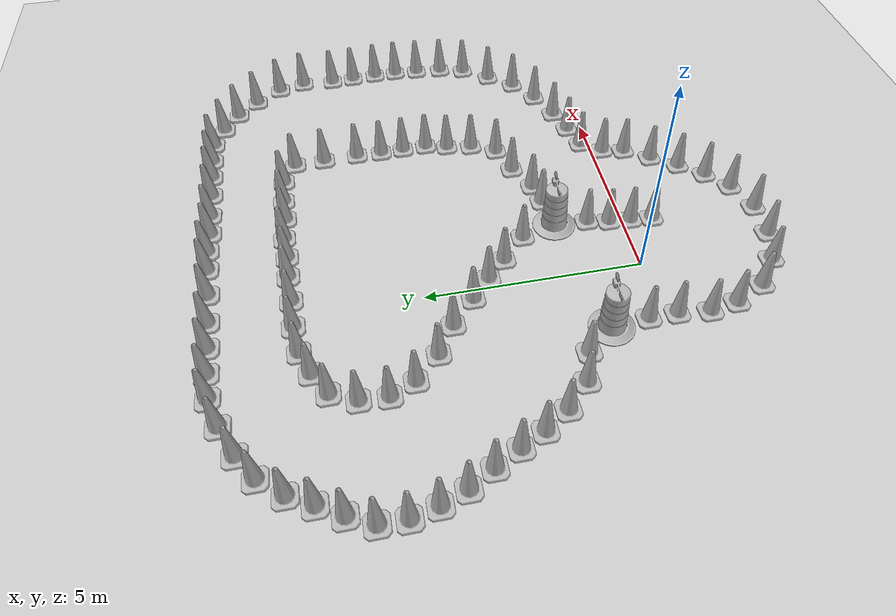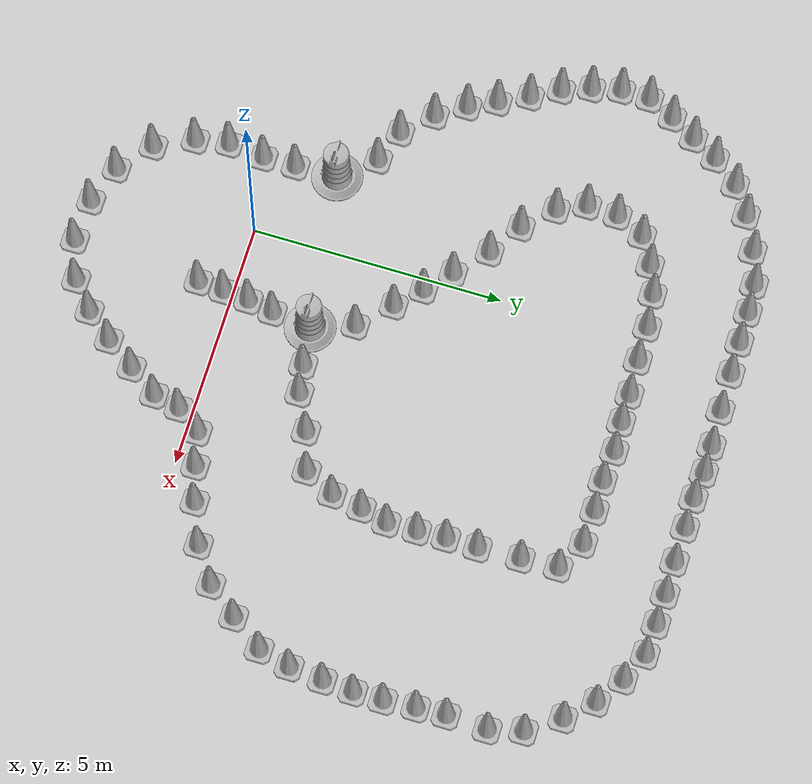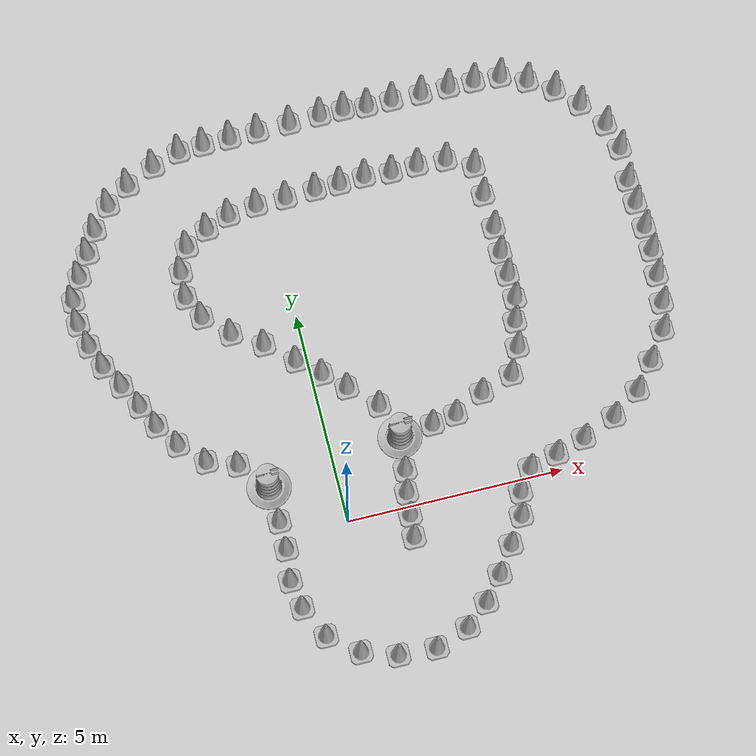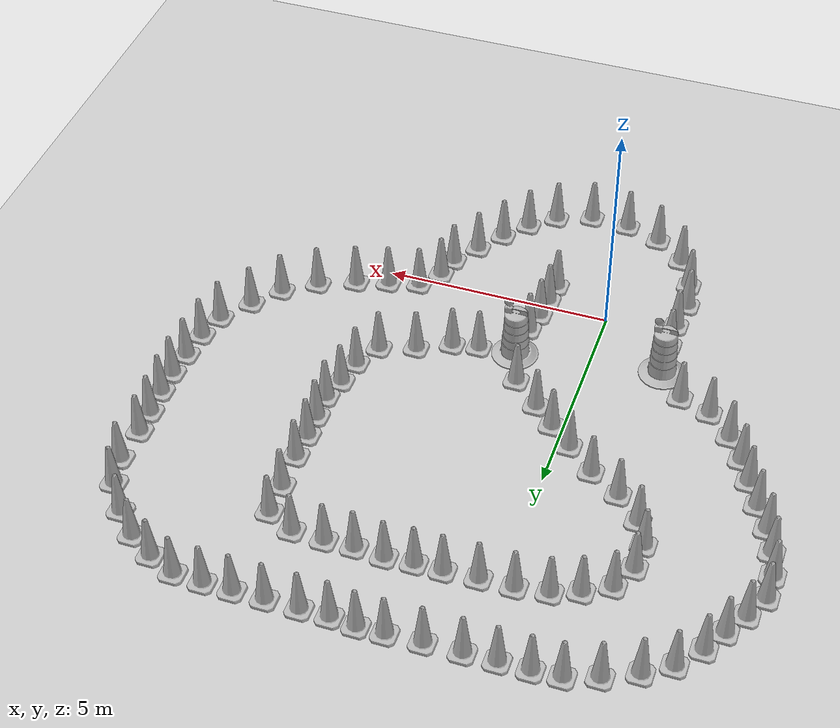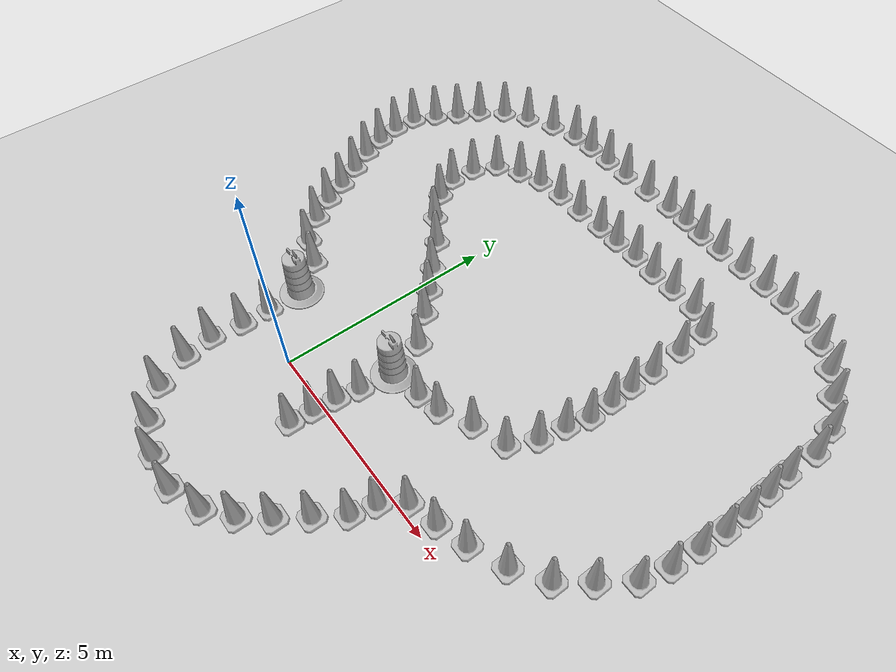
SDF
<sdf version="1.7">
 <world name="default">
  <light name="sun" type="directional">
   <pose>0 0 10 0 -0 0</pose>
   <diffuse>0.8 0.8 0.8 1</diffuse>
   <specular>0.2 0.2 0.2 1</specular>
   <attenuation>
    <range>1000</range>
    <constant>0.9</constant>
    <linear>0.01</linear>
    <quadratic>0.001</quadratic>
   </attenuation>
   <direction>-0.5 0.1 -0.9</direction>
   <spot><inner_angle>0</inner_angle><outer_angle>0</outer_angle><falloff>0</falloff></spot>
  </light>
  <model name="ground_plane">
   <static>1</static>
   <link name="link">
    <collision name="collision">
     <geometry><plane><normal>0 0 1</normal><size>100 100</size></plane></geometry>
     <surface><friction><ode><mu>100</mu><mu2>50</mu2></ode></friction></surface>
    </collision>
    <visual name="visual">
     <cast_shadows>0</cast_shadows>
     <geometry><plane><normal>0 0 1</normal><size>100 100</size></plane></geometry>
     <material>
      <script><uri>file://media/materials/scripts/gazebo.material</uri><name>Gazebo/Grey</name></script>
     </material>
    </visual>
   </link>
  </model>
  <gravity>0 0 -9.8</gravity>
  <magnetic_field>6e-06 2.3e-05 -4.2e-05</magnetic_field>
  <atmosphere type="adiabatic"/>
  <physics type="ode">
   <max_step_size>0.001</max_step_size>
   <real_time_factor>1</real_time_factor>
   <real_time_update_rate>1000</real_time_update_rate>
  </physics>
  <scene><ambient>0.4 0.4 0.4 1</ambient><background>0.7 0.7 0.7 1</background><shadows>1</shadows></scene>
  <audio><device>default</device></audio>
  <spherical_coordinates>
   <surface_model>EARTH_WGS84</surface_model>
   <latitude_deg>0</latitude_deg>
   <longitude_deg>0</longitude_deg>
   <elevation>0</elevation>
   <heading_deg>0</heading_deg>
  </spherical_coordinates>
  <model name="Construction Cone">
   <link name="link">
    <collision name="collision">
     <geometry>
      <mesh><scale>10 10 10</scale><uri>model://construction_cone/meshes/construction_cone.dae</uri></mesh>
     </geometry>
    </collision>
    <visual name="visual">
     <geometry>
      <mesh><scale>10 10 10</scale><uri>model://construction_cone/meshes/construction_cone.dae</uri></mesh>
     </geometry>
    </visual>
    <inertial>
     <inertia><ixx>1</ixx><ixy>0</ixy><ixz>0</ixz><iyy>1</iyy><iyz>0</iyz><izz>1</izz></inertia>
     <mass>1</mass>
    </inertial>
   </link>
   <pose>-1.50858 0.362206 -0 0 -1e-06 0</pose>
  </model>
  <model name="Construction Barrel_0">
   <link name="link">
    <inertial>
     <pose>0 0 0.4 0 -0 0</pose>
     <mass>500</mass>
     <inertia><ixx>51.2096</ixx><iyy>51.2096</iyy><izz>25</izz><ixy>0</ixy><ixz>0</ixz><iyz>0</iyz></inertia>
    </inertial>
    <collision name="collision">
     <geometry><mesh><uri>model://construction_barrel/meshes/construction_barrel.dae</uri></mesh></geometry>
    </collision>
    <visual name="visual">
     <geometry><mesh><uri>model://construction_barrel/meshes/construction_barrel.dae</uri></mesh></geometry>
    </visual>
   </link>
   <pose>1.61149 1.63462 -2e-06 7e-06 -4e-06 -0.000182</pose>
  </model>
  <model name="Construction Cone_0">
   <link name="link">
    <collision name="collision">
     <geometry>
      <mesh><scale>10 10 10</scale><uri>model://construction_cone/meshes/construction_cone.dae</uri></mesh>
     </geometry>
    </collision>
    <visual name="visual">
     <geometry>
      <mesh><scale>10 10 10</scale><uri>model://construction_cone/meshes/construction_cone.dae</uri></mesh>
     </geometry>
    </visual>
    <inertial>
     <inertia><ixx>1</ixx><ixy>0</ixy><ixz>0</ixz><iyy>1</iyy><iyz>0</iyz><izz>1</izz></inertia>
     <mass>1</mass>
    </inertial>
   </link>
   <pose>1.43615 0.328222 -1e-06 3e-06 -1e-06 0</pose>
  </model>
  <model name="Construction Cone_1">
   <link name="link">
    <collision name="collision">
     <geometry>
      <mesh><scale>10 10 10</scale><uri>model://construction_cone/meshes/construction_cone.dae</uri></mesh>
     </geometry>
    </collision>
    <visual name="visual">
     <geometry>
      <mesh><scale>10 10 10</scale><uri>model://construction_cone/meshes/construction_cone.dae</uri></mesh>
     </geometry>
    </visual>
    <inertial>
     <inertia><ixx>1</ixx><ixy>0</ixy><ixz>0</ixz><iyy>1</iyy><iyz>0</iyz><izz>1</izz></inertia>
     <mass>1</mass>
    </inertial>
   </link>
   <pose>-1.58642 -1.01914 -9e-06 -1e-06 -0 -0</pose>
  </model>
  <model name="Construction Cone_2">
   <link name="link">
    <collision name="collision">
     <geometry>
      <mesh><scale>10 10 10</scale><uri>model://construction_cone/meshes/construction_cone.dae</uri></mesh>
     </geometry>
    </collision>
    <visual name="visual">
     <geometry>
      <mesh><scale>10 10 10</scale><uri>model://construction_cone/meshes/construction_cone.dae</uri></mesh>
     </geometry>
    </visual>
    <inertial>
     <inertia><ixx>1</ixx><ixy>0</ixy><ixz>0</ixz><iyy>1</iyy><iyz>0</iyz><izz>1</izz></inertia>
     <mass>1</mass>
    </inertial>
   </link>
   <pose>1.34504 -0.71691 -0 0 -0 0</pose>
  </model>
  <model name="Construction Cone_3">
   <link name="link">
    <collision name="collision">
     <geometry>
      <mesh><scale>10 10 10</scale><uri>model://construction_cone/meshes/construction_cone.dae</uri></mesh>
     </geometry>
    </collision>
    <visual name="visual">
     <geometry>
      <mesh><scale>10 10 10</scale><uri>model://construction_cone/meshes/construction_cone.dae</uri></mesh>
     </geometry>
    </visual>
    <inertial>
     <inertia><ixx>1</ixx><ixy>0</ixy><ixz>0</ixz><iyy>1</iyy><iyz>0</iyz><izz>1</izz></inertia>
     <mass>1</mass>
    </inertial>
   </link>
   <pose>-1.10311 -2.43295 -3e-06 -3e-06 -1e-06 -0</pose>
  </model>
  <model name="Construction Cone_4">
   <link name="link">
    <collision name="collision">
     <geometry>
      <mesh><scale>10 10 10</scale><uri>model://construction_cone/meshes/construction_cone.dae</uri></mesh>
     </geometry>
    </collision>
    <visual name="visual">
     <geometry>
      <mesh><scale>10 10 10</scale><uri>model://construction_cone/meshes/construction_cone.dae</uri></mesh>
     </geometry>
    </visual>
    <inertial>
     <inertia><ixx>1</ixx><ixy>0</ixy><ixz>0</ixz><iyy>1</iyy><iyz>0</iyz><izz>1</izz></inertia>
     <mass>1</mass>
    </inertial>
   </link>
   <pose>0.349808 -3.23868 -6e-06 -4e-06 0 0</pose>
  </model>
  <model name="Construction Cone_5">
   <link name="link">
    <collision name="collision">
     <geometry>
      <mesh><scale>10 10 10</scale><uri>model://construction_cone/meshes/construction_cone.dae</uri></mesh>
     </geometry>
    </collision>
    <visual name="visual">
     <geometry>
      <mesh><scale>10 10 10</scale><uri>model://construction_cone/meshes/construction_cone.dae</uri></mesh>
     </geometry>
    </visual>
    <inertial>
     <inertia><ixx>1</ixx><ixy>0</ixy><ixz>0</ixz><iyy>1</iyy><iyz>0</iyz><izz>1</izz></inertia>
     <mass>1</mass>
    </inertial>
   </link>
   <pose>2 -3 -0 0 -0 0</pose>
  </model>
  <model name="Construction Cone_6">
   <link name="link">
    <collision name="collision">
     <geometry>
      <mesh><scale>10 10 10</scale><uri>model://construction_cone/meshes/construction_cone.dae</uri></mesh>
     </geometry>
    </collision>
    <visual name="visual">
     <geometry>
      <mesh><scale>10 10 10</scale><uri>model://construction_cone/meshes/construction_cone.dae</uri></mesh>
     </geometry>
    </visual>
    <inertial>
     <inertia><ixx>1</ixx><ixy>0</ixy><ixz>0</ixz><iyy>1</iyy><iyz>0</iyz><izz>1</izz></inertia>
     <mass>1</mass>
    </inertial>
   </link>
   <pose>3 -2 -0 0 -0 0</pose>
  </model>
  <model name="Construction Cone_7">
   <link name="link">
    <collision name="collision">
     <geometry>
      <mesh><scale>10 10 10</scale><uri>model://construction_cone/meshes/construction_cone.dae</uri></mesh>
     </geometry>
    </collision>
    <visual name="visual">
     <geometry>
      <mesh><scale>10 10 10</scale><uri>model://construction_cone/meshes/construction_cone.dae</uri></mesh>
     </geometry>
    </visual>
    <inertial>
     <inertia><ixx>1</ixx><ixy>0</ixy><ixz>0</ixz><iyy>1</iyy><iyz>0</iyz><izz>1</izz></inertia>
     <mass>1</mass>
    </inertial>
   </link>
   <pose>3.81489 -0.815615 -6e-06 -4e-06 1e-06 0</pose>
  </model>
  <model name="Construction Cone_9">
   <link name="link">
    <collision name="collision">
     <geometry>
      <mesh><scale>10 10 10</scale><uri>model://construction_cone/meshes/construction_cone.dae</uri></mesh>
     </geometry>
    </collision>
    <visual name="visual">
     <geometry>
      <mesh><scale>10 10 10</scale><uri>model://construction_cone/meshes/construction_cone.dae</uri></mesh>
     </geometry>
    </visual>
    <inertial>
     <inertia><ixx>1</ixx><ixy>0</ixy><ixz>0</ixz><iyy>1</iyy><iyz>0</iyz><izz>1</izz></inertia>
     <mass>1</mass>
    </inertial>
   </link>
   <pose>4.29194 0.215008 -0 0 0 -0.002892</pose>
  </model>
  <model name="Construction Cone_12">
   <link name="link">
    <collision name="collision">
     <geometry>
      <mesh><scale>10 10 10</scale><uri>model://construction_cone/meshes/construction_cone.dae</uri></mesh>
     </geometry>
    </collision>
    <visual name="visual">
     <geometry>
      <mesh><scale>10 10 10</scale><uri>model://construction_cone/meshes/construction_cone.dae</uri></mesh>
     </geometry>
    </visual>
    <inertial>
     <inertia><ixx>1</ixx><ixy>0</ixy><ixz>0</ixz><iyy>1</iyy><iyz>0</iyz><izz>1</izz></inertia>
     <mass>1</mass>
    </inertial>
   </link>
   <pose>2.97197 1.84589 -0 0 -0 0</pose>
  </model>
  <model name="Construction Cone_13">
   <link name="link">
    <collision name="collision">
     <geometry>
      <mesh><scale>10 10 10</scale><uri>model://construction_cone/meshes/construction_cone.dae</uri></mesh>
     </geometry>
    </collision>
    <visual name="visual">
     <geometry>
      <mesh><scale>10 10 10</scale><uri>model://construction_cone/meshes/construction_cone.dae</uri></mesh>
     </geometry>
    </visual>
    <inertial>
     <inertia><ixx>1</ixx><ixy>0</ixy><ixz>0</ixz><iyy>1</iyy><iyz>0</iyz><izz>1</izz></inertia>
     <mass>1</mass>
    </inertial>
   </link>
   <pose>4.44368 2.45442 -0 0 -0 0</pose>
  </model>
  <model name="Construction Cone_15">
   <link name="link">
    <collision name="collision">
     <geometry>
      <mesh><scale>10 10 10</scale><uri>model://construction_cone/meshes/construction_cone.dae</uri></mesh>
     </geometry>
    </collision>
    <visual name="visual">
     <geometry>
      <mesh><scale>10 10 10</scale><uri>model://construction_cone/meshes/construction_cone.dae</uri></mesh>
     </geometry>
    </visual>
    <inertial>
     <inertia><ixx>1</ixx><ixy>0</ixy><ixz>0</ixz><iyy>1</iyy><iyz>0</iyz><izz>1</izz></inertia>
     <mass>1</mass>
    </inertial>
   </link>
   <pose>5.65745 0.599068 -0 0 -0 0</pose>
  </model>
  <model name="Construction Cone_16">
   <link name="link">
    <collision name="collision">
     <geometry>
      <mesh><scale>10 10 10</scale><uri>model://construction_cone/meshes/construction_cone.dae</uri></mesh>
     </geometry>
    </collision>
    <visual name="visual">
     <geometry>
      <mesh><scale>10 10 10</scale><uri>model://construction_cone/meshes/construction_cone.dae</uri></mesh>
     </geometry>
    </visual>
    <inertial>
     <inertia><ixx>1</ixx><ixy>0</ixy><ixz>0</ixz><iyy>1</iyy><iyz>0</iyz><izz>1</izz></inertia>
     <mass>1</mass>
    </inertial>
   </link>
   <pose>7.14122 1.3951 -5e-06 -4e-06 1e-06 0</pose>
  </model>
  <model name="Construction Cone_17">
   <link name="link">
    <collision name="collision">
     <geometry>
      <mesh><scale>10 10 10</scale><uri>model://construction_cone/meshes/construction_cone.dae</uri></mesh>
     </geometry>
    </collision>
    <visual name="visual">
     <geometry>
      <mesh><scale>10 10 10</scale><uri>model://construction_cone/meshes/construction_cone.dae</uri></mesh>
     </geometry>
    </visual>
    <inertial>
     <inertia><ixx>1</ixx><ixy>0</ixy><ixz>0</ixz><iyy>1</iyy><iyz>0</iyz><izz>1</izz></inertia>
     <mass>1</mass>
    </inertial>
   </link>
   <pose>8.09101 2.65771 -0 0 -0 0</pose>
  </model>
  <model name="Construction Cone_19">
   <link name="link">
    <collision name="collision">
     <geometry>
      <mesh><scale>10 10 10</scale><uri>model://construction_cone/meshes/construction_cone.dae</uri></mesh>
     </geometry>
    </collision>
    <visual name="visual">
     <geometry>
      <mesh><scale>10 10 10</scale><uri>model://construction_cone/meshes/construction_cone.dae</uri></mesh>
     </geometry>
    </visual>
    <inertial>
     <inertia><ixx>1</ixx><ixy>0</ixy><ixz>0</ixz><iyy>1</iyy><iyz>0</iyz><izz>1</izz></inertia>
     <mass>1</mass>
    </inertial>
   </link>
   <pose>8.32125 3.97918 -8e-06 -5e-06 -0 -0</pose>
  </model>
  <model name="Construction Cone_14">
   <link name="link">
    <collision name="collision">
     <geometry>
      <mesh><scale>10 10 10</scale><uri>model://construction_cone/meshes/construction_cone.dae</uri></mesh>
     </geometry>
    </collision>
    <visual name="visual">
     <geometry>
      <mesh><scale>10 10 10</scale><uri>model://construction_cone/meshes/construction_cone.dae</uri></mesh>
     </geometry>
    </visual>
    <inertial>
     <inertia><ixx>1</ixx><ixy>0</ixy><ixz>0</ixz><iyy>1</iyy><iyz>0</iyz><izz>1</izz></inertia>
     <mass>1</mass>
    </inertial>
   </link>
   <pose>4.85446 3.67774 -2e-06 -3e-06 -1e-06 -0</pose>
  </model>
  <model name="Construction Cone_8">
   <link name="link">
    <collision name="collision">
     <geometry>
      <mesh><scale>10 10 10</scale><uri>model://construction_cone/meshes/construction_cone.dae</uri></mesh>
     </geometry>
    </collision>
    <visual name="visual">
     <geometry>
      <mesh><scale>10 10 10</scale><uri>model://construction_cone/meshes/construction_cone.dae</uri></mesh>
     </geometry>
    </visual>
    <inertial>
     <inertia><ixx>1</ixx><ixy>0</ixy><ixz>0</ixz><iyy>1</iyy><iyz>0</iyz><izz>1</izz></inertia>
     <mass>1</mass>
    </inertial>
   </link>
   <pose>-0.439786 -2.97166 -0 0 -0 0</pose>
  </model>
  <model name="Construction Cone_10">
   <link name="link">
    <collision name="collision">
     <geometry>
      <mesh><scale>10 10 10</scale><uri>model://construction_cone/meshes/construction_cone.dae</uri></mesh>
     </geometry>
    </collision>
    <visual name="visual">
     <geometry>
      <mesh><scale>10 10 10</scale><uri>model://construction_cone/meshes/construction_cone.dae</uri></mesh>
     </geometry>
    </visual>
    <inertial>
     <inertia><ixx>1</ixx><ixy>0</ixy><ixz>0</ixz><iyy>1</iyy><iyz>0</iyz><izz>1</izz></inertia>
     <mass>1</mass>
    </inertial>
   </link>
   <pose>1.21753 -3.28194 -0 0 -0 0</pose>
  </model>
  <model name="Construction Cone_11">
   <link name="link">
    <collision name="collision">
     <geometry>
      <mesh><scale>10 10 10</scale><uri>model://construction_cone/meshes/construction_cone.dae</uri></mesh>
     </geometry>
    </collision>
    <visual name="visual">
     <geometry>
      <mesh><scale>10 10 10</scale><uri>model://construction_cone/meshes/construction_cone.dae</uri></mesh>
     </geometry>
    </visual>
    <inertial>
     <inertia><ixx>1</ixx><ixy>0</ixy><ixz>0</ixz><iyy>1</iyy><iyz>0</iyz><izz>1</izz></inertia>
     <mass>1</mass>
    </inertial>
   </link>
   <pose>2.54701 -2.54691 -0 0 -0 0</pose>
  </model>
  <model name="Construction Cone_18">
   <link name="link">
    <collision name="collision">
     <geometry>
      <mesh><scale>10 10 10</scale><uri>model://construction_cone/meshes/construction_cone.dae</uri></mesh>
     </geometry>
    </collision>
    <visual name="visual">
     <geometry>
      <mesh><scale>10 10 10</scale><uri>model://construction_cone/meshes/construction_cone.dae</uri></mesh>
     </geometry>
    </visual>
    <inertial>
     <inertia><ixx>1</ixx><ixy>0</ixy><ixz>0</ixz><iyy>1</iyy><iyz>0</iyz><izz>1</izz></inertia>
     <mass>1</mass>
    </inertial>
   </link>
   <pose>3.41673 -1.40396 -0 0 -0 0</pose>
  </model>
  <model name="Construction Cone_20">
   <link name="link">
    <collision name="collision">
     <geometry>
      <mesh><scale>10 10 10</scale><uri>model://construction_cone/meshes/construction_cone.dae</uri></mesh>
     </geometry>
    </collision>
    <visual name="visual">
     <geometry>
      <mesh><scale>10 10 10</scale><uri>model://construction_cone/meshes/construction_cone.dae</uri></mesh>
     </geometry>
    </visual>
    <inertial>
     <inertia><ixx>1</ixx><ixy>0</ixy><ixz>0</ixz><iyy>1</iyy><iyz>0</iyz><izz>1</izz></inertia>
     <mass>1</mass>
    </inertial>
   </link>
   <pose>-1.46811 -1.68302 -9e-06 -5e-06 -0 -0</pose>
  </model>
  <model name="Construction Cone_21">
   <link name="link">
    <collision name="collision">
     <geometry>
      <mesh><scale>10 10 10</scale><uri>model://construction_cone/meshes/construction_cone.dae</uri></mesh>
     </geometry>
    </collision>
    <visual name="visual">
     <geometry>
      <mesh><scale>10 10 10</scale><uri>model://construction_cone/meshes/construction_cone.dae</uri></mesh>
     </geometry>
    </visual>
    <inertial>
     <inertia><ixx>1</ixx><ixy>0</ixy><ixz>0</ixz><iyy>1</iyy><iyz>0</iyz><izz>1</izz></inertia>
     <mass>1</mass>
    </inertial>
   </link>
   <pose>-1.50445 -0.294541 -9e-06 -1e-06 -0 -0</pose>
  </model>
  <model name="Construction Cone_22">
   <link name="link">
    <collision name="collision">
     <geometry>
      <mesh><scale>10 10 10</scale><uri>model://construction_cone/meshes/construction_cone.dae</uri></mesh>
     </geometry>
    </collision>
    <visual name="visual">
     <geometry>
      <mesh><scale>10 10 10</scale><uri>model://construction_cone/meshes/construction_cone.dae</uri></mesh>
     </geometry>
    </visual>
    <inertial>
     <inertia><ixx>1</ixx><ixy>0</ixy><ixz>0</ixz><iyy>1</iyy><iyz>0</iyz><izz>1</izz></inertia>
     <mass>1</mass>
    </inertial>
   </link>
   <pose>3.93882 -0.275644 -0 0 -0 0.000485</pose>
  </model>
  <model name="Construction Cone_23">
   <link name="link">
    <collision name="collision">
     <geometry>
      <mesh><scale>10 10 10</scale><uri>model://construction_cone/meshes/construction_cone.dae</uri></mesh>
     </geometry>
    </collision>
    <visual name="visual">
     <geometry>
      <mesh><scale>10 10 10</scale><uri>model://construction_cone/meshes/construction_cone.dae</uri></mesh>
     </geometry>
    </visual>
    <inertial>
     <inertia><ixx>1</ixx><ixy>0</ixy><ixz>0</ixz><iyy>1</iyy><iyz>0</iyz><izz>1</izz></inertia>
     <mass>1</mass>
    </inertial>
   </link>
   <pose>4.96265 0.387667 -0 0 -0 0</pose>
  </model>
  <model name="Construction Cone_24">
   <link name="link">
    <collision name="collision">
     <geometry>
      <mesh><scale>10 10 10</scale><uri>model://construction_cone/meshes/construction_cone.dae</uri></mesh>
     </geometry>
    </collision>
    <visual name="visual">
     <geometry>
      <mesh><scale>10 10 10</scale><uri>model://construction_cone/meshes/construction_cone.dae</uri></mesh>
     </geometry>
    </visual>
    <inertial>
     <inertia><ixx>1</ixx><ixy>0</ixy><ixz>0</ixz><iyy>1</iyy><iyz>0</iyz><izz>1</izz></inertia>
     <mass>1</mass>
    </inertial>
   </link>
   <pose>3.67747 2.19987 -1e-05 -1e-06 0 0</pose>
  </model>
  <model name="Construction Cone_25">
   <link name="link">
    <collision name="collision">
     <geometry>
      <mesh><scale>10 10 10</scale><uri>model://construction_cone/meshes/construction_cone.dae</uri></mesh>
     </geometry>
    </collision>
    <visual name="visual">
     <geometry>
      <mesh><scale>10 10 10</scale><uri>model://construction_cone/meshes/construction_cone.dae</uri></mesh>
     </geometry>
    </visual>
    <inertial>
     <inertia><ixx>1</ixx><ixy>0</ixy><ixz>0</ixz><iyy>1</iyy><iyz>0</iyz><izz>1</izz></inertia>
     <mass>1</mass>
    </inertial>
   </link>
   <pose>6.45449 0.928592 -1e-05 -1e-06 0 0</pose>
  </model>
  <model name="Construction Cone_26">
   <link name="link">
    <collision name="collision">
     <geometry>
      <mesh><scale>10 10 10</scale><uri>model://construction_cone/meshes/construction_cone.dae</uri></mesh>
     </geometry>
    </collision>
    <visual name="visual">
     <geometry>
      <mesh><scale>10 10 10</scale><uri>model://construction_cone/meshes/construction_cone.dae</uri></mesh>
     </geometry>
    </visual>
    <inertial>
     <inertia><ixx>1</ixx><ixy>0</ixy><ixz>0</ixz><iyy>1</iyy><iyz>0</iyz><izz>1</izz></inertia>
     <mass>1</mass>
    </inertial>
   </link>
   <pose>7.62493 2.00459 -4e-06 4e-06 -1e-06 0</pose>
  </model>
  <model name="Construction Cone_27">
   <link name="link">
    <collision name="collision">
     <geometry>
      <mesh><scale>10 10 10</scale><uri>model://construction_cone/meshes/construction_cone.dae</uri></mesh>
     </geometry>
    </collision>
    <visual name="visual">
     <geometry>
      <mesh><scale>10 10 10</scale><uri>model://construction_cone/meshes/construction_cone.dae</uri></mesh>
     </geometry>
    </visual>
    <inertial>
     <inertia><ixx>1</ixx><ixy>0</ixy><ixz>0</ixz><iyy>1</iyy><iyz>0</iyz><izz>1</izz></inertia>
     <mass>1</mass>
    </inertial>
   </link>
   <pose>4.74587 3.05843 -5e-06 -4e-06 1e-06 0</pose>
  </model>
  <model name="Construction Cone_28">
   <link name="link">
    <collision name="collision">
     <geometry>
      <mesh><scale>10 10 10</scale><uri>model://construction_cone/meshes/construction_cone.dae</uri></mesh>
     </geometry>
    </collision>
    <visual name="visual">
     <geometry>
      <mesh><scale>10 10 10</scale><uri>model://construction_cone/meshes/construction_cone.dae</uri></mesh>
     </geometry>
    </visual>
    <inertial>
     <inertia><ixx>1</ixx><ixy>0</ixy><ixz>0</ixz><iyy>1</iyy><iyz>0</iyz><izz>1</izz></inertia>
     <mass>1</mass>
    </inertial>
   </link>
   <pose>8.255 3.30316 0 -0 -0 -0</pose>
  </model>
  <model name="Construction Cone_29">
   <link name="link">
    <collision name="collision">
     <geometry>
      <mesh><scale>10 10 10</scale><uri>model://construction_cone/meshes/construction_cone.dae</uri></mesh>
     </geometry>
    </collision>
    <visual name="visual">
     <geometry>
      <mesh><scale>10 10 10</scale><uri>model://construction_cone/meshes/construction_cone.dae</uri></mesh>
     </geometry>
    </visual>
    <inertial>
     <inertia><ixx>1</ixx><ixy>0</ixy><ixz>0</ixz><iyy>1</iyy><iyz>0</iyz><izz>1</izz></inertia>
     <mass>1</mass>
    </inertial>
   </link>
   <pose>4.99353 4.2176 -0 0 -0 0</pose>
  </model>
  <model name="Construction Cone_30">
   <link name="link">
    <collision name="collision">
     <geometry>
      <mesh><scale>10 10 10</scale><uri>model://construction_cone/meshes/construction_cone.dae</uri></mesh>
     </geometry>
    </collision>
    <visual name="visual">
     <geometry>
      <mesh><scale>10 10 10</scale><uri>model://construction_cone/meshes/construction_cone.dae</uri></mesh>
     </geometry>
    </visual>
    <inertial>
     <inertia><ixx>1</ixx><ixy>0</ixy><ixz>0</ixz><iyy>1</iyy><iyz>0</iyz><izz>1</izz></inertia>
     <mass>1</mass>
    </inertial>
   </link>
   <pose>8.36914 4.59521 -6e-06 -4e-06 0 0</pose>
  </model>
  <model name="Construction Cone_31">
   <link name="link">
    <collision name="collision">
     <geometry>
      <mesh><scale>10 10 10</scale><uri>model://construction_cone/meshes/construction_cone.dae</uri></mesh>
     </geometry>
    </collision>
    <visual name="visual">
     <geometry>
      <mesh><scale>10 10 10</scale><uri>model://construction_cone/meshes/construction_cone.dae</uri></mesh>
     </geometry>
    </visual>
    <inertial>
     <inertia><ixx>1</ixx><ixy>0</ixy><ixz>0</ixz><iyy>1</iyy><iyz>0</iyz><izz>1</izz></inertia>
     <mass>1</mass>
    </inertial>
   </link>
   <pose>1.38743 -0.192845 -0 0 -0 0</pose>
  </model>
  <model name="Construction Cone_32">
   <link name="link">
    <collision name="collision">
     <geometry>
      <mesh><scale>10 10 10</scale><uri>model://construction_cone/meshes/construction_cone.dae</uri></mesh>
     </geometry>
    </collision>
    <visual name="visual">
     <geometry>
      <mesh><scale>10 10 10</scale><uri>model://construction_cone/meshes/construction_cone.dae</uri></mesh>
     </geometry>
    </visual>
    <inertial>
     <inertia><ixx>1</ixx><ixy>0</ixy><ixz>0</ixz><iyy>1</iyy><iyz>0</iyz><izz>1</izz></inertia>
     <mass>1</mass>
    </inertial>
   </link>
   <pose>1.5335 0.849439 -0 0 -0 0</pose>
  </model>
  <model name="Construction Cone_33">
   <link name="link">
    <collision name="collision">
     <geometry>
      <mesh><scale>10 10 10</scale><uri>model://construction_cone/meshes/construction_cone.dae</uri></mesh>
     </geometry>
    </collision>
    <visual name="visual">
     <geometry>
      <mesh><scale>10 10 10</scale><uri>model://construction_cone/meshes/construction_cone.dae</uri></mesh>
     </geometry>
    </visual>
    <inertial>
     <inertia><ixx>1</ixx><ixy>0</ixy><ixz>0</ixz><iyy>1</iyy><iyz>0</iyz><izz>1</izz></inertia>
     <mass>1</mass>
    </inertial>
   </link>
   <pose>8.29612 6.40467 -3e-06 -3e-06 -1e-06 -0</pose>
  </model>
  <model name="Construction Cone_34">
   <link name="link">
    <collision name="collision">
     <geometry>
      <mesh><scale>10 10 10</scale><uri>model://construction_cone/meshes/construction_cone.dae</uri></mesh>
     </geometry>
    </collision>
    <visual name="visual">
     <geometry>
      <mesh><scale>10 10 10</scale><uri>model://construction_cone/meshes/construction_cone.dae</uri></mesh>
     </geometry>
    </visual>
    <inertial>
     <inertia><ixx>1</ixx><ixy>0</ixy><ixz>0</ixz><iyy>1</iyy><iyz>0</iyz><izz>1</izz></inertia>
     <mass>1</mass>
    </inertial>
   </link>
   <pose>8.34083 7.21964 -0 0 -0 0</pose>
  </model>
  <model name="Construction Cone_35">
   <link name="link">
    <collision name="collision">
     <geometry>
      <mesh><scale>10 10 10</scale><uri>model://construction_cone/meshes/construction_cone.dae</uri></mesh>
     </geometry>
    </collision>
    <visual name="visual">
     <geometry>
      <mesh><scale>10 10 10</scale><uri>model://construction_cone/meshes/construction_cone.dae</uri></mesh>
     </geometry>
    </visual>
    <inertial>
     <inertia><ixx>1</ixx><ixy>0</ixy><ixz>0</ixz><iyy>1</iyy><iyz>0</iyz><izz>1</izz></inertia>
     <mass>1</mass>
    </inertial>
   </link>
   <pose>8.17095 7.88476 -1e-05 0 -0 0</pose>
  </model>
  <model name="Construction Cone_36">
   <link name="link">
    <collision name="collision">
     <geometry>
      <mesh><scale>10 10 10</scale><uri>model://construction_cone/meshes/construction_cone.dae</uri></mesh>
     </geometry>
    </collision>
    <visual name="visual">
     <geometry>
      <mesh><scale>10 10 10</scale><uri>model://construction_cone/meshes/construction_cone.dae</uri></mesh>
     </geometry>
    </visual>
    <inertial>
     <inertia><ixx>1</ixx><ixy>0</ixy><ixz>0</ixz><iyy>1</iyy><iyz>0</iyz><izz>1</izz></inertia>
     <mass>1</mass>
    </inertial>
   </link>
   <pose>7.71925 8.5192 -9e-06 -1e-06 -0 -0</pose>
  </model>
  <model name="Construction Cone_37">
   <link name="link">
    <collision name="collision">
     <geometry>
      <mesh><scale>10 10 10</scale><uri>model://construction_cone/meshes/construction_cone.dae</uri></mesh>
     </geometry>
    </collision>
    <visual name="visual">
     <geometry>
      <mesh><scale>10 10 10</scale><uri>model://construction_cone/meshes/construction_cone.dae</uri></mesh>
     </geometry>
    </visual>
    <inertial>
     <inertia><ixx>1</ixx><ixy>0</ixy><ixz>0</ixz><iyy>1</iyy><iyz>0</iyz><izz>1</izz></inertia>
     <mass>1</mass>
    </inertial>
   </link>
   <pose>7.23112 9.02484 -5e-06 -4e-06 1e-06 0</pose>
  </model>
  <model name="Construction Cone_38">
   <link name="link">
    <collision name="collision">
     <geometry>
      <mesh><scale>10 10 10</scale><uri>model://construction_cone/meshes/construction_cone.dae</uri></mesh>
     </geometry>
    </collision>
    <visual name="visual">
     <geometry>
      <mesh><scale>10 10 10</scale><uri>model://construction_cone/meshes/construction_cone.dae</uri></mesh>
     </geometry>
    </visual>
    <inertial>
     <inertia><ixx>1</ixx><ixy>0</ixy><ixz>0</ixz><iyy>1</iyy><iyz>0</iyz><izz>1</izz></inertia>
     <mass>1</mass>
    </inertial>
   </link>
   <pose>6.66486 9.39048 0 -0 -0 -0</pose>
  </model>
  <model name="Construction Cone_39">
   <link name="link">
    <collision name="collision">
     <geometry>
      <mesh><scale>10 10 10</scale><uri>model://construction_cone/meshes/construction_cone.dae</uri></mesh>
     </geometry>
    </collision>
    <visual name="visual">
     <geometry>
      <mesh><scale>10 10 10</scale><uri>model://construction_cone/meshes/construction_cone.dae</uri></mesh>
     </geometry>
    </visual>
    <inertial>
     <inertia><ixx>1</ixx><ixy>0</ixy><ixz>0</ixz><iyy>1</iyy><iyz>0</iyz><izz>1</izz></inertia>
     <mass>1</mass>
    </inertial>
   </link>
   <pose>6.06943 9.65349 -6e-06 -4e-06 1e-06 0</pose>
  </model>
  <model name="Construction Cone_40">
   <link name="link">
    <collision name="collision">
     <geometry>
      <mesh><scale>10 10 10</scale><uri>model://construction_cone/meshes/construction_cone.dae</uri></mesh>
     </geometry>
    </collision>
    <visual name="visual">
     <geometry>
      <mesh><scale>10 10 10</scale><uri>model://construction_cone/meshes/construction_cone.dae</uri></mesh>
     </geometry>
    </visual>
    <inertial>
     <inertia><ixx>1</ixx><ixy>0</ixy><ixz>0</ixz><iyy>1</iyy><iyz>0</iyz><izz>1</izz></inertia>
     <mass>1</mass>
    </inertial>
   </link>
   <pose>5.43375 9.6839 -0 0 -0 0</pose>
  </model>
  <model name="Construction Cone_41">
   <link name="link">
    <collision name="collision">
     <geometry>
      <mesh><scale>10 10 10</scale><uri>model://construction_cone/meshes/construction_cone.dae</uri></mesh>
     </geometry>
    </collision>
    <visual name="visual">
     <geometry>
      <mesh><scale>10 10 10</scale><uri>model://construction_cone/meshes/construction_cone.dae</uri></mesh>
     </geometry>
    </visual>
    <inertial>
     <inertia><ixx>1</ixx><ixy>0</ixy><ixz>0</ixz><iyy>1</iyy><iyz>0</iyz><izz>1</izz></inertia>
     <mass>1</mass>
    </inertial>
   </link>
   <pose>4.81533 9.68495 -0 0 -0 0</pose>
  </model>
  <model name="Construction Cone_42">
   <link name="link">
    <collision name="collision">
     <geometry>
      <mesh><scale>10 10 10</scale><uri>model://construction_cone/meshes/construction_cone.dae</uri></mesh>
     </geometry>
    </collision>
    <visual name="visual">
     <geometry>
      <mesh><scale>10 10 10</scale><uri>model://construction_cone/meshes/construction_cone.dae</uri></mesh>
     </geometry>
    </visual>
    <inertial>
     <inertia><ixx>1</ixx><ixy>0</ixy><ixz>0</ixz><iyy>1</iyy><iyz>0</iyz><izz>1</izz></inertia>
     <mass>1</mass>
    </inertial>
   </link>
   <pose>4.14486 9.67975 -0 0 -0 0</pose>
  </model>
  <model name="Construction Cone_43">
   <link name="link">
    <collision name="collision">
     <geometry>
      <mesh><scale>10 10 10</scale><uri>model://construction_cone/meshes/construction_cone.dae</uri></mesh>
     </geometry>
    </collision>
    <visual name="visual">
     <geometry>
      <mesh><scale>10 10 10</scale><uri>model://construction_cone/meshes/construction_cone.dae</uri></mesh>
     </geometry>
    </visual>
    <inertial>
     <inertia><ixx>1</ixx><ixy>0</ixy><ixz>0</ixz><iyy>1</iyy><iyz>0</iyz><izz>1</izz></inertia>
     <mass>1</mass>
    </inertial>
   </link>
   <pose>3.43483 9.68563 -0 0 -0 0</pose>
  </model>
  <model name="Construction Cone_44">
   <link name="link">
    <collision name="collision">
     <geometry>
      <mesh><scale>10 10 10</scale><uri>model://construction_cone/meshes/construction_cone.dae</uri></mesh>
     </geometry>
    </collision>
    <visual name="visual">
     <geometry>
      <mesh><scale>10 10 10</scale><uri>model://construction_cone/meshes/construction_cone.dae</uri></mesh>
     </geometry>
    </visual>
    <inertial>
     <inertia><ixx>1</ixx><ixy>0</ixy><ixz>0</ixz><iyy>1</iyy><iyz>0</iyz><izz>1</izz></inertia>
     <mass>1</mass>
    </inertial>
   </link>
   <pose>4.96532 6.01798 -0 0 -0 0</pose>
  </model>
  <model name="Construction Cone_45">
   <link name="link">
    <collision name="collision">
     <geometry>
      <mesh><scale>10 10 10</scale><uri>model://construction_cone/meshes/construction_cone.dae</uri></mesh>
     </geometry>
    </collision>
    <visual name="visual">
     <geometry>
      <mesh><scale>10 10 10</scale><uri>model://construction_cone/meshes/construction_cone.dae</uri></mesh>
     </geometry>
    </visual>
    <inertial>
     <inertia><ixx>1</ixx><ixy>0</ixy><ixz>0</ixz><iyy>1</iyy><iyz>0</iyz><izz>1</izz></inertia>
     <mass>1</mass>
    </inertial>
   </link>
   <pose>4.93141 6.86126 -2e-06 -3e-06 -1e-06 -0</pose>
  </model>
  <model name="Construction Cone_46">
   <link name="link">
    <collision name="collision">
     <geometry>
      <mesh><scale>10 10 10</scale><uri>model://construction_cone/meshes/construction_cone.dae</uri></mesh>
     </geometry>
    </collision>
    <visual name="visual">
     <geometry>
      <mesh><scale>10 10 10</scale><uri>model://construction_cone/meshes/construction_cone.dae</uri></mesh>
     </geometry>
    </visual>
    <inertial>
     <inertia><ixx>1</ixx><ixy>0</ixy><ixz>0</ixz><iyy>1</iyy><iyz>0</iyz><izz>1</izz></inertia>
     <mass>1</mass>
    </inertial>
   </link>
   <pose>4.89809 7.60169 -5e-06 -4e-06 1e-06 0</pose>
  </model>
  <model name="Construction Cone_47">
   <link name="link">
    <collision name="collision">
     <geometry>
      <mesh><scale>10 10 10</scale><uri>model://construction_cone/meshes/construction_cone.dae</uri></mesh>
     </geometry>
    </collision>
    <visual name="visual">
     <geometry>
      <mesh><scale>10 10 10</scale><uri>model://construction_cone/meshes/construction_cone.dae</uri></mesh>
     </geometry>
    </visual>
    <inertial>
     <inertia><ixx>1</ixx><ixy>0</ixy><ixz>0</ixz><iyy>1</iyy><iyz>0</iyz><izz>1</izz></inertia>
     <mass>1</mass>
    </inertial>
   </link>
   <pose>4.29778 7.91397 -8e-06 -5e-06 -0 -0</pose>
  </model>
  <model name="Construction Cone_48">
   <link name="link">
    <collision name="collision">
     <geometry>
      <mesh><scale>10 10 10</scale><uri>model://construction_cone/meshes/construction_cone.dae</uri></mesh>
     </geometry>
    </collision>
    <visual name="visual">
     <geometry>
      <mesh><scale>10 10 10</scale><uri>model://construction_cone/meshes/construction_cone.dae</uri></mesh>
     </geometry>
    </visual>
    <inertial>
     <inertia><ixx>1</ixx><ixy>0</ixy><ixz>0</ixz><iyy>1</iyy><iyz>0</iyz><izz>1</izz></inertia>
     <mass>1</mass>
    </inertial>
   </link>
   <pose>3.60381 7.94248 -0 0 -0 0</pose>
  </model>
  <model name="Construction Cone_49">
   <link name="link">
    <collision name="collision">
     <geometry>
      <mesh><scale>10 10 10</scale><uri>model://construction_cone/meshes/construction_cone.dae</uri></mesh>
     </geometry>
    </collision>
    <visual name="visual">
     <geometry>
      <mesh><scale>10 10 10</scale><uri>model://construction_cone/meshes/construction_cone.dae</uri></mesh>
     </geometry>
    </visual>
    <inertial>
     <inertia><ixx>1</ixx><ixy>0</ixy><ixz>0</ixz><iyy>1</iyy><iyz>0</iyz><izz>1</izz></inertia>
     <mass>1</mass>
    </inertial>
   </link>
   <pose>2.97949 7.92197 -0 0 -0 0</pose>
  </model>
  <model name="Construction Cone_50">
   <link name="link">
    <collision name="collision">
     <geometry>
      <mesh><scale>10 10 10</scale><uri>model://construction_cone/meshes/construction_cone.dae</uri></mesh>
     </geometry>
    </collision>
    <visual name="visual">
     <geometry>
      <mesh><scale>10 10 10</scale><uri>model://construction_cone/meshes/construction_cone.dae</uri></mesh>
     </geometry>
    </visual>
    <inertial>
     <inertia><ixx>1</ixx><ixy>0</ixy><ixz>0</ixz><iyy>1</iyy><iyz>0</iyz><izz>1</izz></inertia>
     <mass>1</mass>
    </inertial>
   </link>
   <pose>2.82271 9.67876 -4e-06 4e-06 -1e-06 0</pose>
  </model>
  <model name="Construction Cone_51">
   <link name="link">
    <collision name="collision">
     <geometry>
      <mesh><scale>10 10 10</scale><uri>model://construction_cone/meshes/construction_cone.dae</uri></mesh>
     </geometry>
    </collision>
    <visual name="visual">
     <geometry>
      <mesh><scale>10 10 10</scale><uri>model://construction_cone/meshes/construction_cone.dae</uri></mesh>
     </geometry>
    </visual>
    <inertial>
     <inertia><ixx>1</ixx><ixy>0</ixy><ixz>0</ixz><iyy>1</iyy><iyz>0</iyz><izz>1</izz></inertia>
     <mass>1</mass>
    </inertial>
   </link>
   <pose>2.34154 7.97075 -0 0 -0 0</pose>
  </model>
  <model name="Construction Cone_52">
   <link name="link">
    <collision name="collision">
     <geometry>
      <mesh><scale>10 10 10</scale><uri>model://construction_cone/meshes/construction_cone.dae</uri></mesh>
     </geometry>
    </collision>
    <visual name="visual">
     <geometry>
      <mesh><scale>10 10 10</scale><uri>model://construction_cone/meshes/construction_cone.dae</uri></mesh>
     </geometry>
    </visual>
    <inertial>
     <inertia><ixx>1</ixx><ixy>0</ixy><ixz>0</ixz><iyy>1</iyy><iyz>0</iyz><izz>1</izz></inertia>
     <mass>1</mass>
    </inertial>
   </link>
   <pose>2.26655 9.72952 -0 0 -0 0</pose>
  </model>
  <model name="Construction Cone_53">
   <link name="link">
    <collision name="collision">
     <geometry>
      <mesh><scale>10 10 10</scale><uri>model://construction_cone/meshes/construction_cone.dae</uri></mesh>
     </geometry>
    </collision>
    <visual name="visual">
     <geometry>
      <mesh><scale>10 10 10</scale><uri>model://construction_cone/meshes/construction_cone.dae</uri></mesh>
     </geometry>
    </visual>
    <inertial>
     <inertia><ixx>1</ixx><ixy>0</ixy><ixz>0</ixz><iyy>1</iyy><iyz>0</iyz><izz>1</izz></inertia>
     <mass>1</mass>
    </inertial>
   </link>
   <pose>1.73595 7.93056 -0 -0 -0 -0</pose>
  </model>
  <model name="Construction Cone_54">
   <link name="link">
    <collision name="collision">
     <geometry>
      <mesh><scale>10 10 10</scale><uri>model://construction_cone/meshes/construction_cone.dae</uri></mesh>
     </geometry>
    </collision>
    <visual name="visual">
     <geometry>
      <mesh><scale>10 10 10</scale><uri>model://construction_cone/meshes/construction_cone.dae</uri></mesh>
     </geometry>
    </visual>
    <inertial>
     <inertia><ixx>1</ixx><ixy>0</ixy><ixz>0</ixz><iyy>1</iyy><iyz>0</iyz><izz>1</izz></inertia>
     <mass>1</mass>
    </inertial>
   </link>
   <pose>1.14894 7.92772 -4e-06 4e-06 -1e-06 0</pose>
  </model>
  <model name="Construction Cone_55">
   <link name="link">
    <collision name="collision">
     <geometry>
      <mesh><scale>10 10 10</scale><uri>model://construction_cone/meshes/construction_cone.dae</uri></mesh>
     </geometry>
    </collision>
    <visual name="visual">
     <geometry>
      <mesh><scale>10 10 10</scale><uri>model://construction_cone/meshes/construction_cone.dae</uri></mesh>
     </geometry>
    </visual>
    <inertial>
     <inertia><ixx>1</ixx><ixy>0</ixy><ixz>0</ixz><iyy>1</iyy><iyz>0</iyz><izz>1</izz></inertia>
     <mass>1</mass>
    </inertial>
   </link>
   <pose>1.69641 9.72068 0 -0 -0 -0</pose>
  </model>
  <model name="Construction Cone_56">
   <link name="link">
    <collision name="collision">
     <geometry>
      <mesh><scale>10 10 10</scale><uri>model://construction_cone/meshes/construction_cone.dae</uri></mesh>
     </geometry>
    </collision>
    <visual name="visual">
     <geometry>
      <mesh><scale>10 10 10</scale><uri>model://construction_cone/meshes/construction_cone.dae</uri></mesh>
     </geometry>
    </visual>
    <inertial>
     <inertia><ixx>1</ixx><ixy>0</ixy><ixz>0</ixz><iyy>1</iyy><iyz>0</iyz><izz>1</izz></inertia>
     <mass>1</mass>
    </inertial>
   </link>
   <pose>0.952207 9.68972 -8e-06 1e-06 -0 0</pose>
  </model>
  <model name="Construction Cone_57">
   <link name="link">
    <collision name="collision">
     <geometry>
      <mesh><scale>10 10 10</scale><uri>model://construction_cone/meshes/construction_cone.dae</uri></mesh>
     </geometry>
    </collision>
    <visual name="visual">
     <geometry>
      <mesh><scale>10 10 10</scale><uri>model://construction_cone/meshes/construction_cone.dae</uri></mesh>
     </geometry>
    </visual>
    <inertial>
     <inertia><ixx>1</ixx><ixy>0</ixy><ixz>0</ixz><iyy>1</iyy><iyz>0</iyz><izz>1</izz></inertia>
     <mass>1</mass>
    </inertial>
   </link>
   <pose>0.175784 9.67322 -0 0 -0 0</pose>
  </model>
  <model name="Construction Cone_58">
   <link name="link">
    <collision name="collision">
     <geometry>
      <mesh><scale>10 10 10</scale><uri>model://construction_cone/meshes/construction_cone.dae</uri></mesh>
     </geometry>
    </collision>
    <visual name="visual">
     <geometry>
      <mesh><scale>10 10 10</scale><uri>model://construction_cone/meshes/construction_cone.dae</uri></mesh>
     </geometry>
    </visual>
    <inertial>
     <inertia><ixx>1</ixx><ixy>0</ixy><ixz>0</ixz><iyy>1</iyy><iyz>0</iyz><izz>1</izz></inertia>
     <mass>1</mass>
    </inertial>
   </link>
   <pose>-0.496271 9.66159 -0 0 -0 0</pose>
  </model>
  <model name="Construction Cone_59">
   <link name="link">
    <collision name="collision">
     <geometry>
      <mesh><scale>10 10 10</scale><uri>model://construction_cone/meshes/construction_cone.dae</uri></mesh>
     </geometry>
    </collision>
    <visual name="visual">
     <geometry>
      <mesh><scale>10 10 10</scale><uri>model://construction_cone/meshes/construction_cone.dae</uri></mesh>
     </geometry>
    </visual>
    <inertial>
     <inertia><ixx>1</ixx><ixy>0</ixy><ixz>0</ixz><iyy>1</iyy><iyz>0</iyz><izz>1</izz></inertia>
     <mass>1</mass>
    </inertial>
   </link>
   <pose>-1.13801 9.65365 -0 0 -0 0</pose>
  </model>
  <model name="Construction Cone_60">
   <link name="link">
    <collision name="collision">
     <geometry>
      <mesh><scale>10 10 10</scale><uri>model://construction_cone/meshes/construction_cone.dae</uri></mesh>
     </geometry>
    </collision>
    <visual name="visual">
     <geometry>
      <mesh><scale>10 10 10</scale><uri>model://construction_cone/meshes/construction_cone.dae</uri></mesh>
     </geometry>
    </visual>
    <inertial>
     <inertia><ixx>1</ixx><ixy>0</ixy><ixz>0</ixz><iyy>1</iyy><iyz>0</iyz><izz>1</izz></inertia>
     <mass>1</mass>
    </inertial>
   </link>
   <pose>-1.73081 9.61376 -0 0 -0 0</pose>
  </model>
  <model name="Construction Cone_61">
   <link name="link">
    <collision name="collision">
     <geometry>
      <mesh><scale>10 10 10</scale><uri>model://construction_cone/meshes/construction_cone.dae</uri></mesh>
     </geometry>
    </collision>
    <visual name="visual">
     <geometry>
      <mesh><scale>10 10 10</scale><uri>model://construction_cone/meshes/construction_cone.dae</uri></mesh>
     </geometry>
    </visual>
    <inertial>
     <inertia><ixx>1</ixx><ixy>0</ixy><ixz>0</ixz><iyy>1</iyy><iyz>0</iyz><izz>1</izz></inertia>
     <mass>1</mass>
    </inertial>
   </link>
   <pose>-2.39577 9.40139 -0 0 -0 0</pose>
  </model>
  <model name="Construction Cone_62">
   <link name="link">
    <collision name="collision">
     <geometry>
      <mesh><scale>10 10 10</scale><uri>model://construction_cone/meshes/construction_cone.dae</uri></mesh>
     </geometry>
    </collision>
    <visual name="visual">
     <geometry>
      <mesh><scale>10 10 10</scale><uri>model://construction_cone/meshes/construction_cone.dae</uri></mesh>
     </geometry>
    </visual>
    <inertial>
     <inertia><ixx>1</ixx><ixy>0</ixy><ixz>0</ixz><iyy>1</iyy><iyz>0</iyz><izz>1</izz></inertia>
     <mass>1</mass>
    </inertial>
   </link>
   <pose>0.434655 7.88982 -9e-06 1e-06 -1e-06 0</pose>
  </model>
  <model name="Construction Cone_63">
   <link name="link">
    <collision name="collision">
     <geometry>
      <mesh><scale>10 10 10</scale><uri>model://construction_cone/meshes/construction_cone.dae</uri></mesh>
     </geometry>
    </collision>
    <visual name="visual">
     <geometry>
      <mesh><scale>10 10 10</scale><uri>model://construction_cone/meshes/construction_cone.dae</uri></mesh>
     </geometry>
    </visual>
    <inertial>
     <inertia><ixx>1</ixx><ixy>0</ixy><ixz>0</ixz><iyy>1</iyy><iyz>0</iyz><izz>1</izz></inertia>
     <mass>1</mass>
    </inertial>
   </link>
   <pose>-0.275901 7.8748 -8e-06 -5e-06 -0 -0</pose>
  </model>
  <model name="Construction Cone_64">
   <link name="link">
    <collision name="collision">
     <geometry>
      <mesh><scale>10 10 10</scale><uri>model://construction_cone/meshes/construction_cone.dae</uri></mesh>
     </geometry>
    </collision>
    <visual name="visual">
     <geometry>
      <mesh><scale>10 10 10</scale><uri>model://construction_cone/meshes/construction_cone.dae</uri></mesh>
     </geometry>
    </visual>
    <inertial>
     <inertia><ixx>1</ixx><ixy>0</ixy><ixz>0</ixz><iyy>1</iyy><iyz>0</iyz><izz>1</izz></inertia>
     <mass>1</mass>
    </inertial>
   </link>
   <pose>-3.07727 9.07697 -6e-06 -4e-06 0 0</pose>
  </model>
  <model name="Construction Cone_65">
   <link name="link">
    <collision name="collision">
     <geometry>
      <mesh><scale>10 10 10</scale><uri>model://construction_cone/meshes/construction_cone.dae</uri></mesh>
     </geometry>
    </collision>
    <visual name="visual">
     <geometry>
      <mesh><scale>10 10 10</scale><uri>model://construction_cone/meshes/construction_cone.dae</uri></mesh>
     </geometry>
    </visual>
    <inertial>
     <inertia><ixx>1</ixx><ixy>0</ixy><ixz>0</ixz><iyy>1</iyy><iyz>0</iyz><izz>1</izz></inertia>
     <mass>1</mass>
    </inertial>
   </link>
   <pose>-3.62795 8.70409 -0 0 -0 0</pose>
  </model>
  <model name="Construction Cone_66">
   <link name="link">
    <collision name="collision">
     <geometry>
      <mesh><scale>10 10 10</scale><uri>model://construction_cone/meshes/construction_cone.dae</uri></mesh>
     </geometry>
    </collision>
    <visual name="visual">
     <geometry>
      <mesh><scale>10 10 10</scale><uri>model://construction_cone/meshes/construction_cone.dae</uri></mesh>
     </geometry>
    </visual>
    <inertial>
     <inertia><ixx>1</ixx><ixy>0</ixy><ixz>0</ixz><iyy>1</iyy><iyz>0</iyz><izz>1</izz></inertia>
     <mass>1</mass>
    </inertial>
   </link>
   <pose>-4.0584 8.17524 -0 0 -0 0</pose>
  </model>
  <model name="Construction Cone_67">
   <link name="link">
    <collision name="collision">
     <geometry>
      <mesh><scale>10 10 10</scale><uri>model://construction_cone/meshes/construction_cone.dae</uri></mesh>
     </geometry>
    </collision>
    <visual name="visual">
     <geometry>
      <mesh><scale>10 10 10</scale><uri>model://construction_cone/meshes/construction_cone.dae</uri></mesh>
     </geometry>
    </visual>
    <inertial>
     <inertia><ixx>1</ixx><ixy>0</ixy><ixz>0</ixz><iyy>1</iyy><iyz>0</iyz><izz>1</izz></inertia>
     <mass>1</mass>
    </inertial>
   </link>
   <pose>-4.34485 7.65362 -4e-06 4e-06 -1e-06 0</pose>
  </model>
  <model name="Construction Cone_68">
   <link name="link">
    <collision name="collision">
     <geometry>
      <mesh><scale>10 10 10</scale><uri>model://construction_cone/meshes/construction_cone.dae</uri></mesh>
     </geometry>
    </collision>
    <visual name="visual">
     <geometry>
      <mesh><scale>10 10 10</scale><uri>model://construction_cone/meshes/construction_cone.dae</uri></mesh>
     </geometry>
    </visual>
    <inertial>
     <inertia><ixx>1</ixx><ixy>0</ixy><ixz>0</ixz><iyy>1</iyy><iyz>0</iyz><izz>1</izz></inertia>
     <mass>1</mass>
    </inertial>
   </link>
   <pose>-4.64841 7.13597 -4e-06 4e-06 -1e-06 0</pose>
  </model>
  <model name="Construction Cone_69">
   <link name="link">
    <collision name="collision">
     <geometry>
      <mesh><scale>10 10 10</scale><uri>model://construction_cone/meshes/construction_cone.dae</uri></mesh>
     </geometry>
    </collision>
    <visual name="visual">
     <geometry>
      <mesh><scale>10 10 10</scale><uri>model://construction_cone/meshes/construction_cone.dae</uri></mesh>
     </geometry>
    </visual>
    <inertial>
     <inertia><ixx>1</ixx><ixy>0</ixy><ixz>0</ixz><iyy>1</iyy><iyz>0</iyz><izz>1</izz></inertia>
     <mass>1</mass>
    </inertial>
   </link>
   <pose>-4.91026 6.59904 -9e-06 -5e-06 -0 -0</pose>
  </model>
  <model name="Construction Cone_70">
   <link name="link">
    <collision name="collision">
     <geometry>
      <mesh><scale>10 10 10</scale><uri>model://construction_cone/meshes/construction_cone.dae</uri></mesh>
     </geometry>
    </collision>
    <visual name="visual">
     <geometry>
      <mesh><scale>10 10 10</scale><uri>model://construction_cone/meshes/construction_cone.dae</uri></mesh>
     </geometry>
    </visual>
    <inertial>
     <inertia><ixx>1</ixx><ixy>0</ixy><ixz>0</ixz><iyy>1</iyy><iyz>0</iyz><izz>1</izz></inertia>
     <mass>1</mass>
    </inertial>
   </link>
   <pose>-4.91951 6.01819 -0 0 -0 0</pose>
  </model>
  <model name="Construction Cone_71">
   <link name="link">
    <collision name="collision">
     <geometry>
      <mesh><scale>10 10 10</scale><uri>model://construction_cone/meshes/construction_cone.dae</uri></mesh>
     </geometry>
    </collision>
    <visual name="visual">
     <geometry>
      <mesh><scale>10 10 10</scale><uri>model://construction_cone/meshes/construction_cone.dae</uri></mesh>
     </geometry>
    </visual>
    <inertial>
     <inertia><ixx>1</ixx><ixy>0</ixy><ixz>0</ixz><iyy>1</iyy><iyz>0</iyz><izz>1</izz></inertia>
     <mass>1</mass>
    </inertial>
   </link>
   <pose>-4.78676 5.4447 -0 -0 -0 -0</pose>
  </model>
  <model name="Construction Cone_72">
   <link name="link">
    <collision name="collision">
     <geometry>
      <mesh><scale>10 10 10</scale><uri>model://construction_cone/meshes/construction_cone.dae</uri></mesh>
     </geometry>
    </collision>
    <visual name="visual">
     <geometry>
      <mesh><scale>10 10 10</scale><uri>model://construction_cone/meshes/construction_cone.dae</uri></mesh>
     </geometry>
    </visual>
    <inertial>
     <inertia><ixx>1</ixx><ixy>0</ixy><ixz>0</ixz><iyy>1</iyy><iyz>0</iyz><izz>1</izz></inertia>
     <mass>1</mass>
    </inertial>
   </link>
   <pose>-4.57705 4.88393 -0 0 -0 0</pose>
  </model>
  <model name="Construction Cone_73">
   <link name="link">
    <collision name="collision">
     <geometry>
      <mesh><scale>10 10 10</scale><uri>model://construction_cone/meshes/construction_cone.dae</uri></mesh>
     </geometry>
    </collision>
    <visual name="visual">
     <geometry>
      <mesh><scale>10 10 10</scale><uri>model://construction_cone/meshes/construction_cone.dae</uri></mesh>
     </geometry>
    </visual>
    <inertial>
     <inertia><ixx>1</ixx><ixy>0</ixy><ixz>0</ixz><iyy>1</iyy><iyz>0</iyz><izz>1</izz></inertia>
     <mass>1</mass>
    </inertial>
   </link>
   <pose>-4.2663 4.33406 -0 0 -0 0</pose>
  </model>
  <model name="Construction Cone_74">
   <link name="link">
    <collision name="collision">
     <geometry>
      <mesh><scale>10 10 10</scale><uri>model://construction_cone/meshes/construction_cone.dae</uri></mesh>
     </geometry>
    </collision>
    <visual name="visual">
     <geometry>
      <mesh><scale>10 10 10</scale><uri>model://construction_cone/meshes/construction_cone.dae</uri></mesh>
     </geometry>
    </visual>
    <inertial>
     <inertia><ixx>1</ixx><ixy>0</ixy><ixz>0</ixz><iyy>1</iyy><iyz>0</iyz><izz>1</izz></inertia>
     <mass>1</mass>
    </inertial>
   </link>
   <pose>-3.96986 3.76236 -6e-06 -4e-06 0 0</pose>
  </model>
  <model name="Construction Cone_75">
   <link name="link">
    <collision name="collision">
     <geometry>
      <mesh><scale>10 10 10</scale><uri>model://construction_cone/meshes/construction_cone.dae</uri></mesh>
     </geometry>
    </collision>
    <visual name="visual">
     <geometry>
      <mesh><scale>10 10 10</scale><uri>model://construction_cone/meshes/construction_cone.dae</uri></mesh>
     </geometry>
    </visual>
    <inertial>
     <inertia><ixx>1</ixx><ixy>0</ixy><ixz>0</ixz><iyy>1</iyy><iyz>0</iyz><izz>1</izz></inertia>
     <mass>1</mass>
    </inertial>
   </link>
   <pose>-3.70204 3.2174 -0 0 -0 0</pose>
  </model>
  <model name="Construction Cone_76">
   <link name="link">
    <collision name="collision">
     <geometry>
      <mesh><scale>10 10 10</scale><uri>model://construction_cone/meshes/construction_cone.dae</uri></mesh>
     </geometry>
    </collision>
    <visual name="visual">
     <geometry>
      <mesh><scale>10 10 10</scale><uri>model://construction_cone/meshes/construction_cone.dae</uri></mesh>
     </geometry>
    </visual>
    <inertial>
     <inertia><ixx>1</ixx><ixy>0</ixy><ixz>0</ixz><iyy>1</iyy><iyz>0</iyz><izz>1</izz></inertia>
     <mass>1</mass>
    </inertial>
   </link>
   <pose>-3.33309 2.65857 -6e-06 2e-06 -0 0</pose>
  </model>
  <model name="Construction Cone_78">
   <link name="link">
    <collision name="collision">
     <geometry>
      <mesh><scale>10 10 10</scale><uri>model://construction_cone/meshes/construction_cone.dae</uri></mesh>
     </geometry>
    </collision>
    <visual name="visual">
     <geometry>
      <mesh><scale>10 10 10</scale><uri>model://construction_cone/meshes/construction_cone.dae</uri></mesh>
     </geometry>
    </visual>
    <inertial>
     <inertia><ixx>1</ixx><ixy>0</ixy><ixz>0</ixz><iyy>1</iyy><iyz>0</iyz><izz>1</izz></inertia>
     <mass>1</mass>
    </inertial>
   </link>
   <pose>-0.9604 7.78693 -9e-06 -1e-06 -0 -0</pose>
  </model>
  <model name="Construction Cone_79">
   <link name="link">
    <collision name="collision">
     <geometry>
      <mesh><scale>10 10 10</scale><uri>model://construction_cone/meshes/construction_cone.dae</uri></mesh>
     </geometry>
    </collision>
    <visual name="visual">
     <geometry>
      <mesh><scale>10 10 10</scale><uri>model://construction_cone/meshes/construction_cone.dae</uri></mesh>
     </geometry>
    </visual>
    <inertial>
     <inertia><ixx>1</ixx><ixy>0</ixy><ixz>0</ixz><iyy>1</iyy><iyz>0</iyz><izz>1</izz></inertia>
     <mass>1</mass>
    </inertial>
   </link>
   <pose>1.32951 2.46996 -6e-06 2e-06 -0 0</pose>
  </model>
  <model name="Construction Cone_80">
   <link name="link">
    <collision name="collision">
     <geometry>
      <mesh><scale>10 10 10</scale><uri>model://construction_cone/meshes/construction_cone.dae</uri></mesh>
     </geometry>
    </collision>
    <visual name="visual">
     <geometry>
      <mesh><scale>10 10 10</scale><uri>model://construction_cone/meshes/construction_cone.dae</uri></mesh>
     </geometry>
    </visual>
    <inertial>
     <inertia><ixx>1</ixx><ixy>0</ixy><ixz>0</ixz><iyy>1</iyy><iyz>0</iyz><izz>1</izz></inertia>
     <mass>1</mass>
    </inertial>
   </link>
   <pose>0.718845 3.05434 -0 0 -1e-06 0</pose>
  </model>
  <model name="Construction Cone_81">
   <link name="link">
    <collision name="collision">
     <geometry>
      <mesh><scale>10 10 10</scale><uri>model://construction_cone/meshes/construction_cone.dae</uri></mesh>
     </geometry>
    </collision>
    <visual name="visual">
     <geometry>
      <mesh><scale>10 10 10</scale><uri>model://construction_cone/meshes/construction_cone.dae</uri></mesh>
     </geometry>
    </visual>
    <inertial>
     <inertia><ixx>1</ixx><ixy>0</ixy><ixz>0</ixz><iyy>1</iyy><iyz>0</iyz><izz>1</izz></inertia>
     <mass>1</mass>
    </inertial>
   </link>
   <pose>0.240598 3.5117 -0 0 -0 0</pose>
  </model>
  <model name="Construction Cone_82">
   <link name="link">
    <collision name="collision">
     <geometry>
      <mesh><scale>10 10 10</scale><uri>model://construction_cone/meshes/construction_cone.dae</uri></mesh>
     </geometry>
    </collision>
    <visual name="visual">
     <geometry>
      <mesh><scale>10 10 10</scale><uri>model://construction_cone/meshes/construction_cone.dae</uri></mesh>
     </geometry>
    </visual>
    <inertial>
     <inertia><ixx>1</ixx><ixy>0</ixy><ixz>0</ixz><iyy>1</iyy><iyz>0</iyz><izz>1</izz></inertia>
     <mass>1</mass>
    </inertial>
   </link>
   <pose>-0.262946 3.96025 -0 0 -0 0</pose>
  </model>
  <model name="Construction Cone_77">
   <link name="link">
    <collision name="collision">
     <geometry>
      <mesh><scale>10 10 10</scale><uri>model://construction_cone/meshes/construction_cone.dae</uri></mesh>
     </geometry>
    </collision>
    <visual name="visual">
     <geometry>
      <mesh><scale>10 10 10</scale><uri>model://construction_cone/meshes/construction_cone.dae</uri></mesh>
     </geometry>
    </visual>
    <inertial>
     <inertia><ixx>1</ixx><ixy>0</ixy><ixz>0</ixz><iyy>1</iyy><iyz>0</iyz><izz>1</izz></inertia>
     <mass>1</mass>
    </inertial>
   </link>
   <pose>-2.79181 2.11434 0 -0 -0 -0</pose>
  </model>
  <model name="Construction Barrel">
   <link name="link">
    <inertial>
     <pose>0 0 0.4 0 -0 0</pose>
     <mass>500</mass>
     <inertia><ixx>51.2096</ixx><iyy>51.2096</iyy><izz>25</izz><ixy>0</ixy><ixz>0</ixz><iyz>0</iyz></inertia>
    </inertial>
    <collision name="collision">
     <geometry><mesh><uri>model://construction_barrel/meshes/construction_barrel.dae</uri></mesh></geometry>
    </collision>
    <visual name="visual">
     <geometry><mesh><uri>model://construction_barrel/meshes/construction_barrel.dae</uri></mesh></geometry>
    </visual>
   </link>
   <pose>-1.54892 1.20006 -1e-06 1e-06 -9e-06 -2.7e-05</pose>
  </model>
  <model name="Construction Cone_83">
   <link name="link">
    <collision name="collision">
     <geometry>
      <mesh><scale>10 10 10</scale><uri>model://construction_cone/meshes/construction_cone.dae</uri></mesh>
     </geometry>
    </collision>
    <visual name="visual">
     <geometry>
      <mesh><scale>10 10 10</scale><uri>model://construction_cone/meshes/construction_cone.dae</uri></mesh>
     </geometry>
    </visual>
    <inertial>
     <inertia><ixx>1</ixx><ixy>0</ixy><ixz>0</ixz><iyy>1</iyy><iyz>0</iyz><izz>1</izz></inertia>
     <mass>1</mass>
    </inertial>
   </link>
   <pose>-2.10738 1.86915 -0 0 -0 0</pose>
  </model>
  <model name="Construction Cone_84">
   <link name="link">
    <collision name="collision">
     <geometry>
      <mesh><scale>10 10 10</scale><uri>model://construction_cone/meshes/construction_cone.dae</uri></mesh>
     </geometry>
    </collision>
    <visual name="visual">
     <geometry>
      <mesh><scale>10 10 10</scale><uri>model://construction_cone/meshes/construction_cone.dae</uri></mesh>
     </geometry>
    </visual>
    <inertial>
     <inertia><ixx>1</ixx><ixy>0</ixy><ixz>0</ixz><iyy>1</iyy><iyz>0</iyz><izz>1</izz></inertia>
     <mass>1</mass>
    </inertial>
   </link>
   <pose>-0.882947 4.51478 -6e-06 -4e-06 1e-06 0</pose>
  </model>
  <model name="Construction Cone_85">
   <link name="link">
    <collision name="collision">
     <geometry>
      <mesh><scale>10 10 10</scale><uri>model://construction_cone/meshes/construction_cone.dae</uri></mesh>
     </geometry>
    </collision>
    <visual name="visual">
     <geometry>
      <mesh><scale>10 10 10</scale><uri>model://construction_cone/meshes/construction_cone.dae</uri></mesh>
     </geometry>
    </visual>
    <inertial>
     <inertia><ixx>1</ixx><ixy>0</ixy><ixz>0</ixz><iyy>1</iyy><iyz>0</iyz><izz>1</izz></inertia>
     <mass>1</mass>
    </inertial>
   </link>
   <pose>-1.52717 7.57291 -0 0 -0 0</pose>
  </model>
  <model name="Construction Cone_86">
   <link name="link">
    <collision name="collision">
     <geometry>
      <mesh><scale>10 10 10</scale><uri>model://construction_cone/meshes/construction_cone.dae</uri></mesh>
     </geometry>
    </collision>
    <visual name="visual">
     <geometry>
      <mesh><scale>10 10 10</scale><uri>model://construction_cone/meshes/construction_cone.dae</uri></mesh>
     </geometry>
    </visual>
    <inertial>
     <inertia><ixx>1</ixx><ixy>0</ixy><ixz>0</ixz><iyy>1</iyy><iyz>0</iyz><izz>1</izz></inertia>
     <mass>1</mass>
    </inertial>
   </link>
   <pose>-2.07448 7.25622 -0 -0 -0 -0</pose>
  </model>
  <model name="Construction Cone_87">
   <link name="link">
    <collision name="collision">
     <geometry>
      <mesh><scale>10 10 10</scale><uri>model://construction_cone/meshes/construction_cone.dae</uri></mesh>
     </geometry>
    </collision>
    <visual name="visual">
     <geometry>
      <mesh><scale>10 10 10</scale><uri>model://construction_cone/meshes/construction_cone.dae</uri></mesh>
     </geometry>
    </visual>
    <inertial>
     <inertia><ixx>1</ixx><ixy>0</ixy><ixz>0</ixz><iyy>1</iyy><iyz>0</iyz><izz>1</izz></inertia>
     <mass>1</mass>
    </inertial>
   </link>
   <pose>-2.34241 6.68171 -1e-05 -1e-06 0 0</pose>
  </model>
  <model name="Construction Cone_88">
   <link name="link">
    <collision name="collision">
     <geometry>
      <mesh><scale>10 10 10</scale><uri>model://construction_cone/meshes/construction_cone.dae</uri></mesh>
     </geometry>
    </collision>
    <visual name="visual">
     <geometry>
      <mesh><scale>10 10 10</scale><uri>model://construction_cone/meshes/construction_cone.dae</uri></mesh>
     </geometry>
    </visual>
    <inertial>
     <inertia><ixx>1</ixx><ixy>0</ixy><ixz>0</ixz><iyy>1</iyy><iyz>0</iyz><izz>1</izz></inertia>
     <mass>1</mass>
    </inertial>
   </link>
   <pose>-2.37159 6.05694 0 -0 -0 -0</pose>
  </model>
  <model name="Construction Cone_89">
   <link name="link">
    <collision name="collision">
     <geometry>
      <mesh><scale>10 10 10</scale><uri>model://construction_cone/meshes/construction_cone.dae</uri></mesh>
     </geometry>
    </collision>
    <visual name="visual">
     <geometry>
      <mesh><scale>10 10 10</scale><uri>model://construction_cone/meshes/construction_cone.dae</uri></mesh>
     </geometry>
    </visual>
    <inertial>
     <inertia><ixx>1</ixx><ixy>0</ixy><ixz>0</ixz><iyy>1</iyy><iyz>0</iyz><izz>1</izz></inertia>
     <mass>1</mass>
    </inertial>
   </link>
   <pose>-2.11552 5.49839 -0 0 -0 0</pose>
  </model>
  <model name="Construction Cone_90">
   <link name="link">
    <collision name="collision">
     <geometry>
      <mesh><scale>10 10 10</scale><uri>model://construction_cone/meshes/construction_cone.dae</uri></mesh>
     </geometry>
    </collision>
    <visual name="visual">
     <geometry>
      <mesh><scale>10 10 10</scale><uri>model://construction_cone/meshes/construction_cone.dae</uri></mesh>
     </geometry>
    </visual>
    <inertial>
     <inertia><ixx>1</ixx><ixy>0</ixy><ixz>0</ixz><iyy>1</iyy><iyz>0</iyz><izz>1</izz></inertia>
     <mass>1</mass>
    </inertial>
   </link>
   <pose>-1.56213 4.9433 -0 0 -0 0</pose>
  </model>
  <model name="Construction Cone_91">
   <link name="link">
    <collision name="collision">
     <geometry>
      <mesh><scale>10 10 10</scale><uri>model://construction_cone/meshes/construction_cone.dae</uri></mesh>
     </geometry>
    </collision>
    <visual name="visual">
     <geometry>
      <mesh><scale>10 10 10</scale><uri>model://construction_cone/meshes/construction_cone.dae</uri></mesh>
     </geometry>
    </visual>
    <inertial>
     <inertia><ixx>1</ixx><ixy>0</ixy><ixz>0</ixz><iyy>1</iyy><iyz>0</iyz><izz>1</izz></inertia>
     <mass>1</mass>
    </inertial>
   </link>
   <pose>2.39725 1.74316 -0 0 -0 0</pose>
  </model>
  <model name="Construction Cone_92">
   <link name="link">
    <collision name="collision">
     <geometry>
      <mesh><scale>10 10 10</scale><uri>model://construction_cone/meshes/construction_cone.dae</uri></mesh>
     </geometry>
    </collision>
    <visual name="visual">
     <geometry>
      <mesh><scale>10 10 10</scale><uri>model://construction_cone/meshes/construction_cone.dae</uri></mesh>
     </geometry>
    </visual>
    <inertial>
     <inertia><ixx>1</ixx><ixy>0</ixy><ixz>0</ixz><iyy>1</iyy><iyz>0</iyz><izz>1</izz></inertia>
     <mass>1</mass>
    </inertial>
   </link>
   <pose>8.36464 5.18252 -2e-06 -3e-06 -1e-06 -0</pose>
  </model>
  <model name="Construction Cone_93">
   <link name="link">
    <collision name="collision">
     <geometry>
      <mesh><scale>10 10 10</scale><uri>model://construction_cone/meshes/construction_cone.dae</uri></mesh>
     </geometry>
    </collision>
    <visual name="visual">
     <geometry>
      <mesh><scale>10 10 10</scale><uri>model://construction_cone/meshes/construction_cone.dae</uri></mesh>
     </geometry>
    </visual>
    <inertial>
     <inertia><ixx>1</ixx><ixy>0</ixy><ixz>0</ixz><iyy>1</iyy><iyz>0</iyz><izz>1</izz></inertia>
     <mass>1</mass>
    </inertial>
   </link>
   <pose>8.32361 5.81693 -1e-05 0 -0 0</pose>
  </model>
  <model name="Construction Cone_95">
   <link name="link">
    <collision name="collision">
     <geometry>
      <mesh><scale>10 10 10</scale><uri>model://construction_cone/meshes/construction_cone.dae</uri></mesh>
     </geometry>
    </collision>
    <visual name="visual">
     <geometry>
      <mesh><scale>10 10 10</scale><uri>model://construction_cone/meshes/construction_cone.dae</uri></mesh>
     </geometry>
    </visual>
    <inertial>
     <inertia><ixx>1</ixx><ixy>0</ixy><ixz>0</ixz><iyy>1</iyy><iyz>0</iyz><izz>1</izz></inertia>
     <mass>1</mass>
    </inertial>
   </link>
   <pose>4.95655 5.3906 -0 0 -0 0</pose>
  </model>
  <model name="Construction Cone_94">
   <link name="link">
    <collision name="collision">
     <geometry>
      <mesh><scale>10 10 10</scale><uri>model://construction_cone/meshes/construction_cone.dae</uri></mesh>
     </geometry>
    </collision>
    <visual name="visual">
     <geometry>
      <mesh><scale>10 10 10</scale><uri>model://construction_cone/meshes/construction_cone.dae</uri></mesh>
     </geometry>
    </visual>
    <inertial>
     <inertia><ixx>1</ixx><ixy>0</ixy><ixz>0</ixz><iyy>1</iyy><iyz>0</iyz><izz>1</izz></inertia>
     <mass>1</mass>
    </inertial>
   </link>
   <pose>4.9777 4.81859 -0 0 -1e-06 0</pose>
  </model>
 </world>
</sdf>
